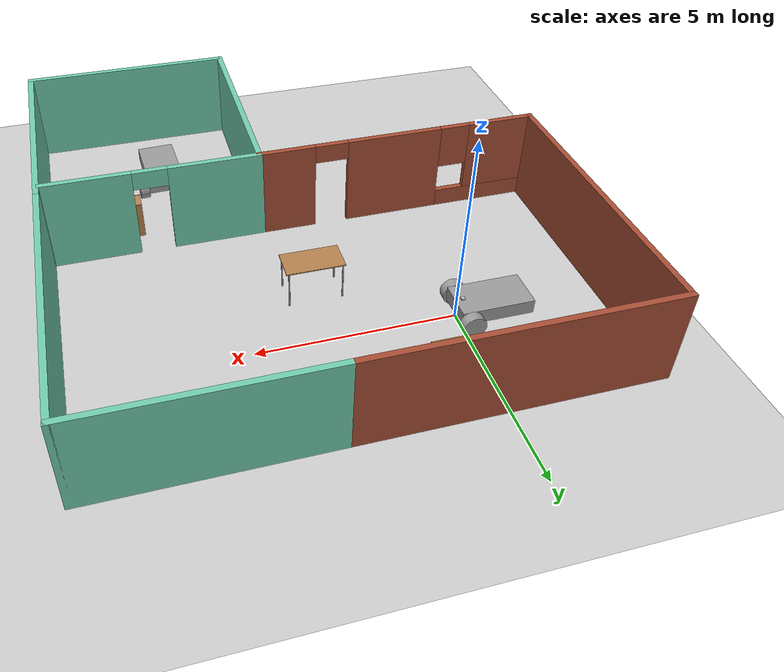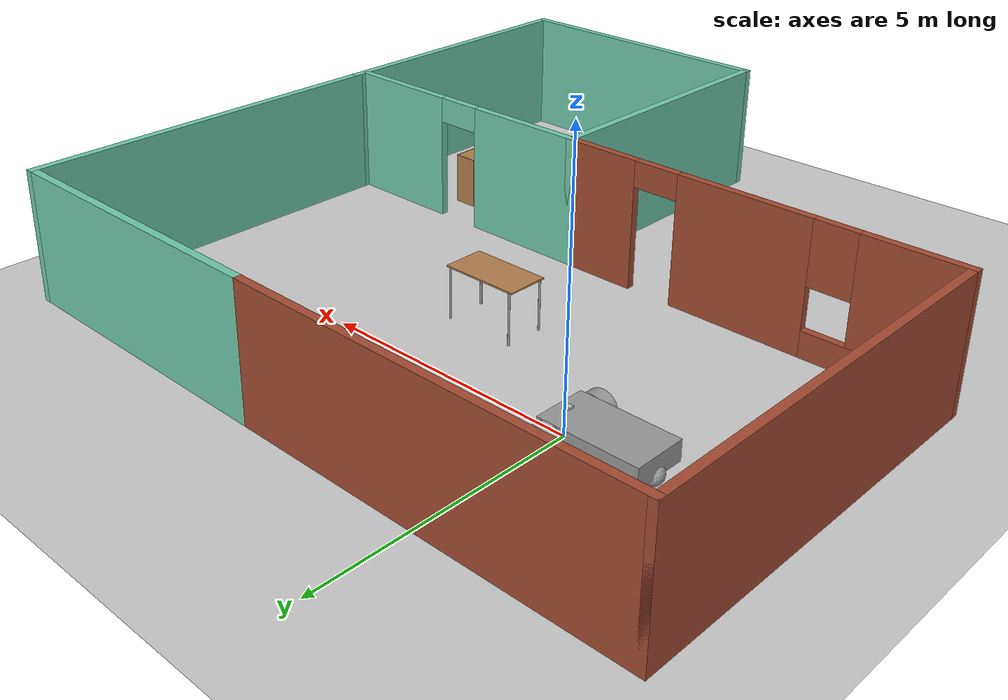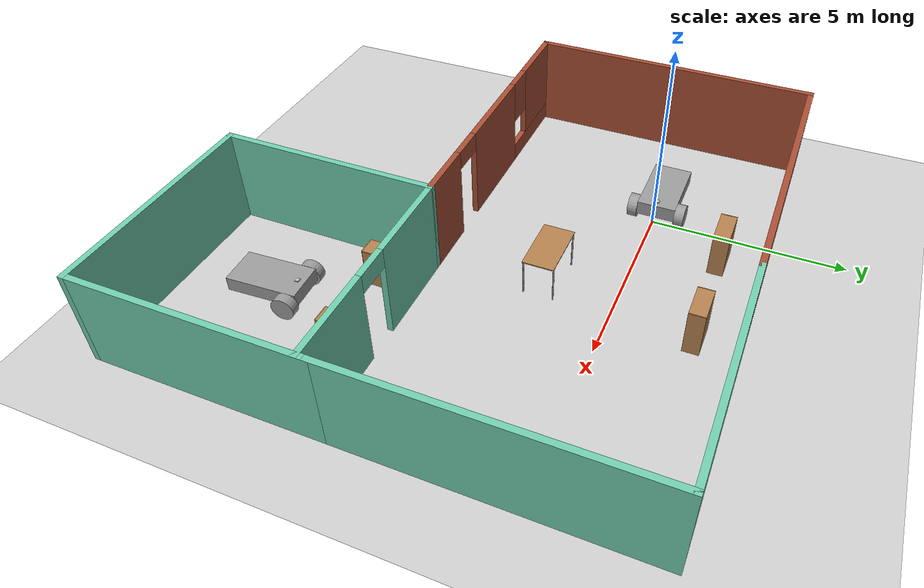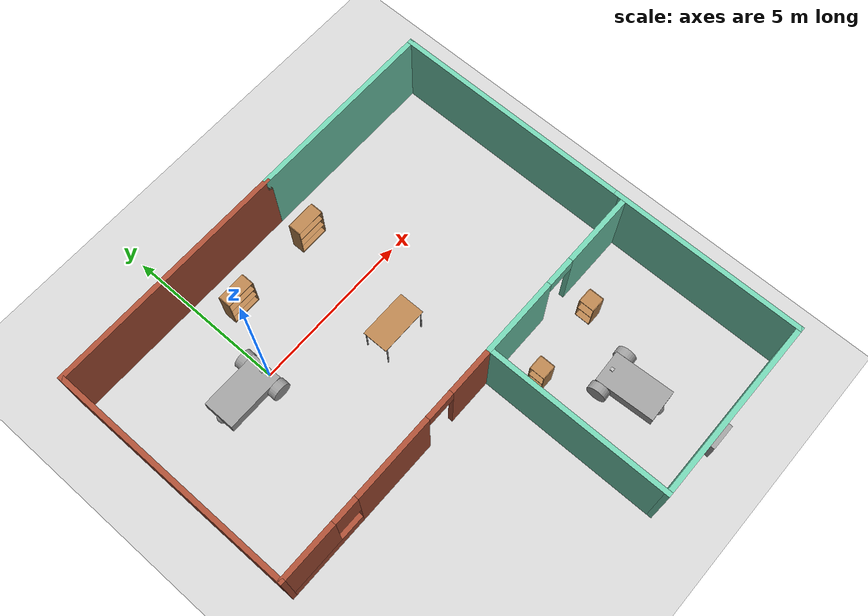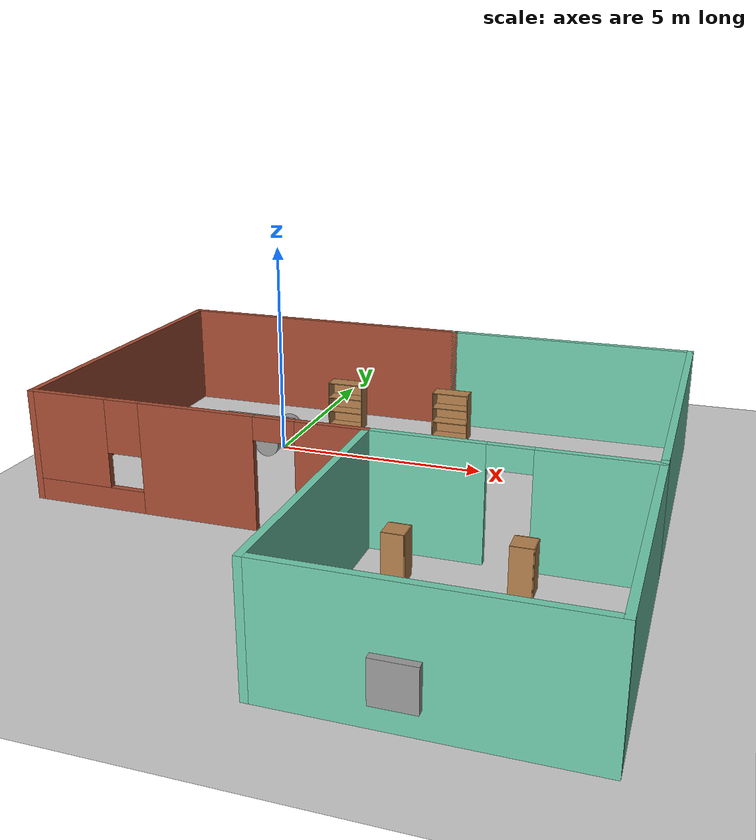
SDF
<sdf version="1.6">
 <world name="default">
  <plugin name="hello" filename="libhello.so"/>
  <light name="sun" type="directional">
   <pose>0 0 10 0 -0 0</pose>
   <diffuse>0.8 0.8 0.8 1</diffuse>
   <specular>0.2 0.2 0.2 1</specular>
   <attenuation>
    <range>1000</range>
    <constant>0.9</constant>
    <linear>0.01</linear>
    <quadratic>0.001</quadratic>
   </attenuation>
   <direction>-0.5 0.1 -0.9</direction>
  </light>
  <model name="ground_plane">
   <static>1</static>
   <link name="link">
    <collision name="collision">
     <geometry><plane><normal>0 0 1</normal><size>100 100</size></plane></geometry>
     <surface>
      <contact><collide_bitmask>65535</collide_bitmask></contact>
      <friction><ode><mu>100</mu><mu2>50</mu2></ode></friction>
     </surface>
    </collision>
    <visual name="visual">
     <cast_shadows>0</cast_shadows>
     <geometry><plane><normal>0 0 1</normal><size>100 100</size></plane></geometry>
     <material>
      <script><uri>file://media/materials/scripts/gazebo.material</uri><name>Gazebo/Grey</name></script>
     </material>
    </visual>
   </link>
  </model>
  <gravity>0 0 -9.8</gravity>
  <magnetic_field>6e-06 2.3e-05 -4.2e-05</magnetic_field>
  <atmosphere type="adiabatic"/>
  <physics name="default_physics" default="0" type="ode">
   <max_step_size>0.001</max_step_size>
   <real_time_factor>1</real_time_factor>
   <real_time_update_rate>1000</real_time_update_rate>
  </physics>
  <scene><ambient>0.4 0.4 0.4 1</ambient><background>0.7 0.7 0.7 1</background><shadows>1</shadows></scene>
  <audio><device>default</device></audio>
  <spherical_coordinates>
   <surface_model>EARTH_WGS84</surface_model>
   <latitude_deg>0</latitude_deg>
   <longitude_deg>0</longitude_deg>
   <elevation>0</elevation>
   <heading_deg>0</heading_deg>
  </spherical_coordinates>
  <model name="Building">
   <link name="Wall_0">
    <pose>-2.925 6.6 0 0 -0 0</pose>
    <visual name="Wall_0_Visual">
     <pose>0 0 1.25 0 -0 0</pose>
     <geometry><box><size>7.5 0.15 2.5</size></box></geometry>
     <material>
      <script><uri>file://media/materials/scripts/gazebo.material</uri><name>Gazebo/Bricks</name></script>
      <ambient>1 1 1 1</ambient>
     </material>
     <meta><layer>0</layer></meta>
    </visual>
    <collision name="Wall_0_Collision">
     <pose>0 0 1.25 0 -0 0</pose>
     <geometry><box><size>7.5 0.15 2.5</size></box></geometry>
     <surface>
      <friction>
       <ode><mu>1</mu><mu2>1</mu2><fdir1>0 0 0</fdir1><slip1>0</slip1><slip2>0</slip2></ode>
       <torsional>
        <coefficient>1</coefficient>
        <patch_radius>0</patch_radius>
        <surface_radius>0</surface_radius>
        <use_patch_radius>1</use_patch_radius>
        <ode><slip>0</slip></ode>
       </torsional>
      </friction>
      <bounce><restitution_coefficient>0</restitution_coefficient><threshold>1e+06</threshold></bounce>
      <contact>
       <collide_without_contact>0</collide_without_contact>
       <collide_without_contact_bitmask>1</collide_without_contact_bitmask>
       <collide_bitmask>1</collide_bitmask>
       <ode>
        <soft_cfm>0</soft_cfm>
        <soft_erp>0.2</soft_erp>
        <kp>1e+13</kp>
        <kd>1</kd>
        <max_vel>0.01</max_vel>
        <min_depth>0</min_depth>
       </ode>
       <bullet>
        <split_impulse>1</split_impulse>
        <split_impulse_penetration_threshold>-0.01</split_impulse_penetration_threshold>
        <soft_cfm>0</soft_cfm>
        <soft_erp>0.2</soft_erp>
        <kp>1e+13</kp>
        <kd>1</kd>
       </bullet>
      </contact>
     </surface>
    </collision>
   </link>
   <link name="Wall_1">
    <pose>3.675 6.6 0 0 -0 0</pose>
    <visual name="Wall_1_Visual">
     <pose>0 0 1.25 0 -0 0</pose>
     <geometry><box><size>6 0.15 2.5</size></box></geometry>
     <material>
      <script><uri>file://media/materials/scripts/gazebo.material</uri><name>Gazebo/Grey</name></script>
      <ambient>0.435294 0.796078 0.67451 1</ambient>
     </material>
     <meta><layer>0</layer></meta>
    </visual>
    <collision name="Wall_1_Collision">
     <pose>0 0 1.25 0 -0 0</pose>
     <geometry><box><size>6 0.15 2.5</size></box></geometry>
     <surface>
      <friction>
       <ode><mu>1</mu><mu2>1</mu2><fdir1>0 0 0</fdir1><slip1>0</slip1><slip2>0</slip2></ode>
       <torsional>
        <coefficient>1</coefficient>
        <patch_radius>0</patch_radius>
        <surface_radius>0</surface_radius>
        <use_patch_radius>1</use_patch_radius>
        <ode><slip>0</slip></ode>
       </torsional>
      </friction>
      <bounce><restitution_coefficient>0</restitution_coefficient><threshold>1e+06</threshold></bounce>
      <contact>
       <collide_without_contact>0</collide_without_contact>
       <collide_without_contact_bitmask>1</collide_without_contact_bitmask>
       <collide_bitmask>1</collide_bitmask>
       <ode>
        <soft_cfm>0</soft_cfm>
        <soft_erp>0.2</soft_erp>
        <kp>1e+13</kp>
        <kd>1</kd>
        <max_vel>0.01</max_vel>
        <min_depth>0</min_depth>
       </ode>
       <bullet>
        <split_impulse>1</split_impulse>
        <split_impulse_penetration_threshold>-0.01</split_impulse_penetration_threshold>
        <soft_cfm>0</soft_cfm>
        <soft_erp>0.2</soft_erp>
        <kp>1e+13</kp>
        <kd>1</kd>
       </bullet>
      </contact>
     </surface>
    </collision>
   </link>
   <link name="Wall_14">
    <pose>3.8 -1 0 0 -0 0</pose>
    <visual name="Wall_14_Visual_2">
     <pose>0.031268 0 2.25 0 -0 0</pose>
     <geometry><box><size>0.9 0.15 0.5</size></box></geometry>
     <material>
      <script><uri>file://media/materials/scripts/gazebo.material</uri><name>Gazebo/Grey</name></script>
      <ambient>0.435294 0.796078 0.67451 1</ambient>
     </material>
     <meta><layer>0</layer></meta>
    </visual>
    <visual name="Wall_14_Visual_0">
     <pose>-1.64687 0 1.25 0 -0 0</pose>
     <geometry><box><size>2.45627 0.15 2.5</size></box></geometry>
     <material>
      <script><uri>file://media/materials/scripts/gazebo.material</uri><name>Gazebo/Grey</name></script>
      <ambient>0.435294 0.796078 0.67451 1</ambient>
     </material>
     <meta><layer>0</layer></meta>
    </visual>
    <visual name="Wall_14_Visual_1">
     <pose>1.67813 0 1.25 0 -0 0</pose>
     <geometry><box><size>2.39373 0.15 2.5</size></box></geometry>
     <material>
      <script><uri>file://media/materials/scripts/gazebo.material</uri><name>Gazebo/Grey</name></script>
      <ambient>0.435294 0.796078 0.67451 1</ambient>
     </material>
     <meta><layer>0</layer></meta>
    </visual>
    <collision name="Wall_14_Collision_0">
     <pose>-1.64687 0 1.25 0 -0 0</pose>
     <geometry><box><size>2.45627 0.15 2.5</size></box></geometry>
     <surface>
      <friction>
       <ode><mu>1</mu><mu2>1</mu2><fdir1>0 0 0</fdir1><slip1>0</slip1><slip2>0</slip2></ode>
       <torsional>
        <coefficient>1</coefficient>
        <patch_radius>0</patch_radius>
        <surface_radius>0</surface_radius>
        <use_patch_radius>1</use_patch_radius>
        <ode><slip>0</slip></ode>
       </torsional>
      </friction>
      <bounce><restitution_coefficient>0</restitution_coefficient><threshold>1e+06</threshold></bounce>
      <contact>
       <collide_without_contact>0</collide_without_contact>
       <collide_without_contact_bitmask>1</collide_without_contact_bitmask>
       <collide_bitmask>1</collide_bitmask>
       <ode>
        <soft_cfm>0</soft_cfm>
        <soft_erp>0.2</soft_erp>
        <kp>1e+13</kp>
        <kd>1</kd>
        <max_vel>0.01</max_vel>
        <min_depth>0</min_depth>
       </ode>
       <bullet>
        <split_impulse>1</split_impulse>
        <split_impulse_penetration_threshold>-0.01</split_impulse_penetration_threshold>
        <soft_cfm>0</soft_cfm>
        <soft_erp>0.2</soft_erp>
        <kp>1e+13</kp>
        <kd>1</kd>
       </bullet>
      </contact>
     </surface>
    </collision>
    <collision name="Wall_14_Collision_1">
     <pose>1.67813 0 1.25 0 -0 0</pose>
     <geometry><box><size>2.39373 0.15 2.5</size></box></geometry>
     <surface>
      <friction>
       <ode><mu>1</mu><mu2>1</mu2><fdir1>0 0 0</fdir1><slip1>0</slip1><slip2>0</slip2></ode>
       <torsional>
        <coefficient>1</coefficient>
        <patch_radius>0</patch_radius>
        <surface_radius>0</surface_radius>
        <use_patch_radius>1</use_patch_radius>
        <ode><slip>0</slip></ode>
       </torsional>
      </friction>
      <bounce><restitution_coefficient>0</restitution_coefficient><threshold>1e+06</threshold></bounce>
      <contact>
       <collide_without_contact>0</collide_without_contact>
       <collide_without_contact_bitmask>1</collide_without_contact_bitmask>
       <collide_bitmask>1</collide_bitmask>
       <ode>
        <soft_cfm>0</soft_cfm>
        <soft_erp>0.2</soft_erp>
        <kp>1e+13</kp>
        <kd>1</kd>
        <max_vel>0.01</max_vel>
        <min_depth>0</min_depth>
       </ode>
       <bullet>
        <split_impulse>1</split_impulse>
        <split_impulse_penetration_threshold>-0.01</split_impulse_penetration_threshold>
        <soft_cfm>0</soft_cfm>
        <soft_erp>0.2</soft_erp>
        <kp>1e+13</kp>
        <kd>1</kd>
       </bullet>
      </contact>
     </surface>
    </collision>
    <collision name="Wall_14_Collision_2">
     <pose>0.031268 0 2.25 0 -0 0</pose>
     <geometry><box><size>0.9 0.15 0.5</size></box></geometry>
     <surface>
      <friction>
       <ode><mu>1</mu><mu2>1</mu2><fdir1>0 0 0</fdir1><slip1>0</slip1><slip2>0</slip2></ode>
       <torsional>
        <coefficient>1</coefficient>
        <patch_radius>0</patch_radius>
        <surface_radius>0</surface_radius>
        <use_patch_radius>1</use_patch_radius>
        <ode><slip>0</slip></ode>
       </torsional>
      </friction>
      <bounce><restitution_coefficient>0</restitution_coefficient><threshold>1e+06</threshold></bounce>
      <contact>
       <collide_without_contact>0</collide_without_contact>
       <collide_without_contact_bitmask>1</collide_without_contact_bitmask>
       <collide_bitmask>1</collide_bitmask>
       <ode>
        <soft_cfm>0</soft_cfm>
        <soft_erp>0.2</soft_erp>
        <kp>1e+13</kp>
        <kd>1</kd>
        <max_vel>0.01</max_vel>
        <min_depth>0</min_depth>
       </ode>
       <bullet>
        <split_impulse>1</split_impulse>
        <split_impulse_penetration_threshold>-0.01</split_impulse_penetration_threshold>
        <soft_cfm>0</soft_cfm>
        <soft_erp>0.2</soft_erp>
        <kp>1e+13</kp>
        <kd>1</kd>
       </bullet>
      </contact>
     </surface>
    </collision>
   </link>
   <link name="Wall_2">
    <pose>6.6 2.925 0 0 0 -1.5708</pose>
    <visual name="Wall_2_Visual">
     <pose>0 0 1.25 0 -0 0</pose>
     <geometry><box><size>7.5 0.15 2.5</size></box></geometry>
     <material>
      <script><uri>file://media/materials/scripts/gazebo.material</uri><name>Gazebo/Grey</name></script>
      <ambient>0.435294 0.796078 0.67451 1</ambient>
     </material>
     <meta><layer>0</layer></meta>
    </visual>
    <collision name="Wall_2_Collision">
     <pose>0 0 1.25 0 -0 0</pose>
     <geometry><box><size>7.5 0.15 2.5</size></box></geometry>
     <surface>
      <friction>
       <ode><mu>1</mu><mu2>1</mu2><fdir1>0 0 0</fdir1><slip1>0</slip1><slip2>0</slip2></ode>
       <torsional>
        <coefficient>1</coefficient>
        <patch_radius>0</patch_radius>
        <surface_radius>0</surface_radius>
        <use_patch_radius>1</use_patch_radius>
        <ode><slip>0</slip></ode>
       </torsional>
      </friction>
      <bounce><restitution_coefficient>0</restitution_coefficient><threshold>1e+06</threshold></bounce>
      <contact>
       <collide_without_contact>0</collide_without_contact>
       <collide_without_contact_bitmask>1</collide_without_contact_bitmask>
       <collide_bitmask>1</collide_bitmask>
       <ode>
        <soft_cfm>0</soft_cfm>
        <soft_erp>0.2</soft_erp>
        <kp>1e+13</kp>
        <kd>1</kd>
        <max_vel>0.01</max_vel>
        <min_depth>0</min_depth>
       </ode>
       <bullet>
        <split_impulse>1</split_impulse>
        <split_impulse_penetration_threshold>-0.01</split_impulse_penetration_threshold>
        <soft_cfm>0</soft_cfm>
        <soft_erp>0.2</soft_erp>
        <kp>1e+13</kp>
        <kd>1</kd>
       </bullet>
      </contact>
     </surface>
    </collision>
   </link>
   <link name="Wall_3">
    <pose>6.6 -3.675 0 0 0 -1.5708</pose>
    <visual name="Wall_3_Visual">
     <pose>0 0 1.25 0 -0 0</pose>
     <geometry><box><size>6 0.15 2.5</size></box></geometry>
     <material>
      <script><uri>file://media/materials/scripts/gazebo.material</uri><name>Gazebo/Grey</name></script>
      <ambient>0.435294 0.796078 0.67451 1</ambient>
     </material>
     <meta><layer>0</layer></meta>
    </visual>
    <collision name="Wall_3_Collision">
     <pose>0 0 1.25 0 -0 0</pose>
     <geometry><box><size>6 0.15 2.5</size></box></geometry>
     <surface>
      <friction>
       <ode><mu>1</mu><mu2>1</mu2><fdir1>0 0 0</fdir1><slip1>0</slip1><slip2>0</slip2></ode>
       <torsional>
        <coefficient>1</coefficient>
        <patch_radius>0</patch_radius>
        <surface_radius>0</surface_radius>
        <use_patch_radius>1</use_patch_radius>
        <ode><slip>0</slip></ode>
       </torsional>
      </friction>
      <bounce><restitution_coefficient>0</restitution_coefficient><threshold>1e+06</threshold></bounce>
      <contact>
       <collide_without_contact>0</collide_without_contact>
       <collide_without_contact_bitmask>1</collide_without_contact_bitmask>
       <collide_bitmask>1</collide_bitmask>
       <ode>
        <soft_cfm>0</soft_cfm>
        <soft_erp>0.2</soft_erp>
        <kp>1e+13</kp>
        <kd>1</kd>
        <max_vel>0.01</max_vel>
        <min_depth>0</min_depth>
       </ode>
       <bullet>
        <split_impulse>1</split_impulse>
        <split_impulse_penetration_threshold>-0.01</split_impulse_penetration_threshold>
        <soft_cfm>0</soft_cfm>
        <soft_erp>0.2</soft_erp>
        <kp>1e+13</kp>
        <kd>1</kd>
       </bullet>
      </contact>
     </surface>
    </collision>
   </link>
   <link name="Wall_4">
    <pose>3.8 -6.6 0 0 -0 3.14159</pose>
    <visual name="Wall_4_Visual">
     <pose>0 0 1.25 0 -0 0</pose>
     <geometry><box><size>5.75 0.15 2.5</size></box></geometry>
     <material>
      <script><uri>file://media/materials/scripts/gazebo.material</uri><name>Gazebo/Grey</name></script>
      <ambient>0.435294 0.796078 0.67451 1</ambient>
     </material>
     <meta><layer>0</layer></meta>
    </visual>
    <collision name="Wall_4_Collision">
     <pose>0 0 1.25 0 -0 0</pose>
     <geometry><box><size>5.75 0.15 2.5</size></box></geometry>
     <surface>
      <friction>
       <ode><mu>1</mu><mu2>1</mu2><fdir1>0 0 0</fdir1><slip1>0</slip1><slip2>0</slip2></ode>
       <torsional>
        <coefficient>1</coefficient>
        <patch_radius>0</patch_radius>
        <surface_radius>0</surface_radius>
        <use_patch_radius>1</use_patch_radius>
        <ode><slip>0</slip></ode>
       </torsional>
      </friction>
      <bounce><restitution_coefficient>0</restitution_coefficient><threshold>1e+06</threshold></bounce>
      <contact>
       <collide_without_contact>0</collide_without_contact>
       <collide_without_contact_bitmask>1</collide_without_contact_bitmask>
       <collide_bitmask>1</collide_bitmask>
       <ode>
        <soft_cfm>0</soft_cfm>
        <soft_erp>0.2</soft_erp>
        <kp>1e+13</kp>
        <kd>1</kd>
        <max_vel>0.01</max_vel>
        <min_depth>0</min_depth>
       </ode>
       <bullet>
        <split_impulse>1</split_impulse>
        <split_impulse_penetration_threshold>-0.01</split_impulse_penetration_threshold>
        <soft_cfm>0</soft_cfm>
        <soft_erp>0.2</soft_erp>
        <kp>1e+13</kp>
        <kd>1</kd>
       </bullet>
      </contact>
     </surface>
    </collision>
   </link>
   <link name="Wall_5">
    <pose>1 -3.8 0 0 -0 1.5708</pose>
    <visual name="Wall_5_Visual">
     <pose>0 0 1.25 0 -0 0</pose>
     <geometry><box><size>5.75 0.15 2.5</size></box></geometry>
     <material>
      <script><uri>file://media/materials/scripts/gazebo.material</uri><name>Gazebo/Grey</name></script>
      <ambient>0.435294 0.796078 0.67451 1</ambient>
     </material>
     <meta><layer>0</layer></meta>
    </visual>
    <collision name="Wall_5_Collision">
     <pose>0 0 1.25 0 -0 0</pose>
     <geometry><box><size>5.75 0.15 2.5</size></box></geometry>
     <surface>
      <friction>
       <ode><mu>1</mu><mu2>1</mu2><fdir1>0 0 0</fdir1><slip1>0</slip1><slip2>0</slip2></ode>
       <torsional>
        <coefficient>1</coefficient>
        <patch_radius>0</patch_radius>
        <surface_radius>0</surface_radius>
        <use_patch_radius>1</use_patch_radius>
        <ode><slip>0</slip></ode>
       </torsional>
      </friction>
      <bounce><restitution_coefficient>0</restitution_coefficient><threshold>1e+06</threshold></bounce>
      <contact>
       <collide_without_contact>0</collide_without_contact>
       <collide_without_contact_bitmask>1</collide_without_contact_bitmask>
       <collide_bitmask>1</collide_bitmask>
       <ode>
        <soft_cfm>0</soft_cfm>
        <soft_erp>0.2</soft_erp>
        <kp>1e+13</kp>
        <kd>1</kd>
        <max_vel>0.01</max_vel>
        <min_depth>0</min_depth>
       </ode>
       <bullet>
        <split_impulse>1</split_impulse>
        <split_impulse_penetration_threshold>-0.01</split_impulse_penetration_threshold>
        <soft_cfm>0</soft_cfm>
        <soft_erp>0.2</soft_erp>
        <kp>1e+13</kp>
        <kd>1</kd>
       </bullet>
      </contact>
     </surface>
    </collision>
   </link>
   <link name="Wall_6">
    <pose>-2.8 -1 0 0 -0 3.14159</pose>
    <visual name="Wall_6_Visual_0">
     <pose>-3.0921 0 1.25 0 -0 0</pose>
     <geometry><box><size>1.56581 0.15 2.5</size></box></geometry>
     <material>
      <script><uri>file://media/materials/scripts/gazebo.material</uri><name>Gazebo/Bricks</name></script>
      <ambient>1 1 1 1</ambient>
     </material>
     <meta><layer>0</layer></meta>
    </visual>
    <visual name="Wall_6_Visual_1">
     <pose>-0.105844 0 1.25 0 -0 0</pose>
     <geometry><box><size>2.6067 0.15 2.5</size></box></geometry>
     <material>
      <script><uri>file://media/materials/scripts/gazebo.material</uri><name>Gazebo/Bricks</name></script>
      <ambient>1 1 1 1</ambient>
     </material>
     <meta><layer>0</layer></meta>
    </visual>
    <visual name="Wall_6_Visual_2">
     <pose>2.53625 0 0.25 0 -0 0</pose>
     <geometry><box><size>2.6775 0.15 0.5</size></box></geometry>
     <material>
      <script><uri>file://media/materials/scripts/gazebo.material</uri><name>Gazebo/Bricks</name></script>
      <ambient>1 1 1 1</ambient>
     </material>
     <meta><layer>0</layer></meta>
    </visual>
    <visual name="Wall_6_Visual_3">
     <pose>2.93625 0 1.5 0 -0 0</pose>
     <geometry><box><size>1.8775 0.15 2</size></box></geometry>
     <material>
      <script><uri>file://media/materials/scripts/gazebo.material</uri><name>Gazebo/Bricks</name></script>
      <ambient>1 1 1 1</ambient>
     </material>
     <meta><layer>0</layer></meta>
    </visual>
    <visual name="Wall_6_Visual_4">
     <pose>1.5975 0 1.9 0 -0 0</pose>
     <geometry><box><size>0.8 0.15 1.2</size></box></geometry>
     <material>
      <script><uri>file://media/materials/scripts/gazebo.material</uri><name>Gazebo/Bricks</name></script>
      <ambient>1 1 1 1</ambient>
     </material>
     <meta><layer>0</layer></meta>
    </visual>
    <visual name="Wall_6_Visual_5">
     <pose>-1.85919 0 2.25 0 -0 0</pose>
     <geometry><box><size>0.9 0.15 0.5</size></box></geometry>
     <material>
      <script><uri>file://media/materials/scripts/gazebo.material</uri><name>Gazebo/Bricks</name></script>
      <ambient>1 1 1 1</ambient>
     </material>
     <meta><layer>0</layer></meta>
    </visual>
    <collision name="Wall_6_Collision_0">
     <pose>-3.0921 0 1.25 0 -0 0</pose>
     <geometry><box><size>1.56581 0.15 2.5</size></box></geometry>
     <surface>
      <friction>
       <ode><mu>1</mu><mu2>1</mu2><fdir1>0 0 0</fdir1><slip1>0</slip1><slip2>0</slip2></ode>
       <torsional>
        <coefficient>1</coefficient>
        <patch_radius>0</patch_radius>
        <surface_radius>0</surface_radius>
        <use_patch_radius>1</use_patch_radius>
        <ode><slip>0</slip></ode>
       </torsional>
      </friction>
      <bounce><restitution_coefficient>0</restitution_coefficient><threshold>1e+06</threshold></bounce>
      <contact>
       <collide_without_contact>0</collide_without_contact>
       <collide_without_contact_bitmask>1</collide_without_contact_bitmask>
       <collide_bitmask>1</collide_bitmask>
       <ode>
        <soft_cfm>0</soft_cfm>
        <soft_erp>0.2</soft_erp>
        <kp>1e+13</kp>
        <kd>1</kd>
        <max_vel>0.01</max_vel>
        <min_depth>0</min_depth>
       </ode>
       <bullet>
        <split_impulse>1</split_impulse>
        <split_impulse_penetration_threshold>-0.01</split_impulse_penetration_threshold>
        <soft_cfm>0</soft_cfm>
        <soft_erp>0.2</soft_erp>
        <kp>1e+13</kp>
        <kd>1</kd>
       </bullet>
      </contact>
     </surface>
    </collision>
    <collision name="Wall_6_Collision_1">
     <pose>-0.105844 0 1.25 0 -0 0</pose>
     <geometry><box><size>2.6067 0.15 2.5</size></box></geometry>
     <surface>
      <friction>
       <ode><mu>1</mu><mu2>1</mu2><fdir1>0 0 0</fdir1><slip1>0</slip1><slip2>0</slip2></ode>
       <torsional>
        <coefficient>1</coefficient>
        <patch_radius>0</patch_radius>
        <surface_radius>0</surface_radius>
        <use_patch_radius>1</use_patch_radius>
        <ode><slip>0</slip></ode>
       </torsional>
      </friction>
      <bounce><restitution_coefficient>0</restitution_coefficient><threshold>1e+06</threshold></bounce>
      <contact>
       <collide_without_contact>0</collide_without_contact>
       <collide_without_contact_bitmask>1</collide_without_contact_bitmask>
       <collide_bitmask>1</collide_bitmask>
       <ode>
        <soft_cfm>0</soft_cfm>
        <soft_erp>0.2</soft_erp>
        <kp>1e+13</kp>
        <kd>1</kd>
        <max_vel>0.01</max_vel>
        <min_depth>0</min_depth>
       </ode>
       <bullet>
        <split_impulse>1</split_impulse>
        <split_impulse_penetration_threshold>-0.01</split_impulse_penetration_threshold>
        <soft_cfm>0</soft_cfm>
        <soft_erp>0.2</soft_erp>
        <kp>1e+13</kp>
        <kd>1</kd>
       </bullet>
      </contact>
     </surface>
    </collision>
    <collision name="Wall_6_Collision_2">
     <pose>2.53625 0 0.25 0 -0 0</pose>
     <geometry><box><size>2.6775 0.15 0.5</size></box></geometry>
     <surface>
      <friction>
       <ode><mu>1</mu><mu2>1</mu2><fdir1>0 0 0</fdir1><slip1>0</slip1><slip2>0</slip2></ode>
       <torsional>
        <coefficient>1</coefficient>
        <patch_radius>0</patch_radius>
        <surface_radius>0</surface_radius>
        <use_patch_radius>1</use_patch_radius>
        <ode><slip>0</slip></ode>
       </torsional>
      </friction>
      <bounce><restitution_coefficient>0</restitution_coefficient><threshold>1e+06</threshold></bounce>
      <contact>
       <collide_without_contact>0</collide_without_contact>
       <collide_without_contact_bitmask>1</collide_without_contact_bitmask>
       <collide_bitmask>1</collide_bitmask>
       <ode>
        <soft_cfm>0</soft_cfm>
        <soft_erp>0.2</soft_erp>
        <kp>1e+13</kp>
        <kd>1</kd>
        <max_vel>0.01</max_vel>
        <min_depth>0</min_depth>
       </ode>
       <bullet>
        <split_impulse>1</split_impulse>
        <split_impulse_penetration_threshold>-0.01</split_impulse_penetration_threshold>
        <soft_cfm>0</soft_cfm>
        <soft_erp>0.2</soft_erp>
        <kp>1e+13</kp>
        <kd>1</kd>
       </bullet>
      </contact>
     </surface>
    </collision>
    <collision name="Wall_6_Collision_4">
     <pose>1.5975 0 1.9 0 -0 0</pose>
     <geometry><box><size>0.8 0.15 1.2</size></box></geometry>
     <surface>
      <friction>
       <ode><mu>1</mu><mu2>1</mu2><fdir1>0 0 0</fdir1><slip1>0</slip1><slip2>0</slip2></ode>
       <torsional>
        <coefficient>1</coefficient>
        <patch_radius>0</patch_radius>
        <surface_radius>0</surface_radius>
        <use_patch_radius>1</use_patch_radius>
        <ode><slip>0</slip></ode>
       </torsional>
      </friction>
      <bounce><restitution_coefficient>0</restitution_coefficient><threshold>1e+06</threshold></bounce>
      <contact>
       <collide_without_contact>0</collide_without_contact>
       <collide_without_contact_bitmask>1</collide_without_contact_bitmask>
       <collide_bitmask>1</collide_bitmask>
       <ode>
        <soft_cfm>0</soft_cfm>
        <soft_erp>0.2</soft_erp>
        <kp>1e+13</kp>
        <kd>1</kd>
        <max_vel>0.01</max_vel>
        <min_depth>0</min_depth>
       </ode>
       <bullet>
        <split_impulse>1</split_impulse>
        <split_impulse_penetration_threshold>-0.01</split_impulse_penetration_threshold>
        <soft_cfm>0</soft_cfm>
        <soft_erp>0.2</soft_erp>
        <kp>1e+13</kp>
        <kd>1</kd>
       </bullet>
      </contact>
     </surface>
    </collision>
    <collision name="Wall_6_Collision_3">
     <pose>2.93625 0 1.5 0 -0 0</pose>
     <geometry><box><size>1.8775 0.15 2</size></box></geometry>
     <surface>
      <friction>
       <ode><mu>1</mu><mu2>1</mu2><fdir1>0 0 0</fdir1><slip1>0</slip1><slip2>0</slip2></ode>
       <torsional>
        <coefficient>1</coefficient>
        <patch_radius>0</patch_radius>
        <surface_radius>0</surface_radius>
        <use_patch_radius>1</use_patch_radius>
        <ode><slip>0</slip></ode>
       </torsional>
      </friction>
      <bounce><restitution_coefficient>0</restitution_coefficient><threshold>1e+06</threshold></bounce>
      <contact>
       <collide_without_contact>0</collide_without_contact>
       <collide_without_contact_bitmask>1</collide_without_contact_bitmask>
       <collide_bitmask>1</collide_bitmask>
       <ode>
        <soft_cfm>0</soft_cfm>
        <soft_erp>0.2</soft_erp>
        <kp>1e+13</kp>
        <kd>1</kd>
        <max_vel>0.01</max_vel>
        <min_depth>0</min_depth>
       </ode>
       <bullet>
        <split_impulse>1</split_impulse>
        <split_impulse_penetration_threshold>-0.01</split_impulse_penetration_threshold>
        <soft_cfm>0</soft_cfm>
        <soft_erp>0.2</soft_erp>
        <kp>1e+13</kp>
        <kd>1</kd>
       </bullet>
      </contact>
     </surface>
    </collision>
    <collision name="Wall_6_Collision_5">
     <pose>-1.85919 0 2.25 0 -0 0</pose>
     <geometry><box><size>0.9 0.15 0.5</size></box></geometry>
     <surface>
      <friction>
       <ode><mu>1</mu><mu2>1</mu2><fdir1>0 0 0</fdir1><slip1>0</slip1><slip2>0</slip2></ode>
       <torsional>
        <coefficient>1</coefficient>
        <patch_radius>0</patch_radius>
        <surface_radius>0</surface_radius>
        <use_patch_radius>1</use_patch_radius>
        <ode><slip>0</slip></ode>
       </torsional>
      </friction>
      <bounce><restitution_coefficient>0</restitution_coefficient><threshold>1e+06</threshold></bounce>
      <contact>
       <collide_without_contact>0</collide_without_contact>
       <collide_without_contact_bitmask>1</collide_without_contact_bitmask>
       <collide_bitmask>1</collide_bitmask>
       <ode>
        <soft_cfm>0</soft_cfm>
        <soft_erp>0.2</soft_erp>
        <kp>1e+13</kp>
        <kd>1</kd>
        <max_vel>0.01</max_vel>
        <min_depth>0</min_depth>
       </ode>
       <bullet>
        <split_impulse>1</split_impulse>
        <split_impulse_penetration_threshold>-0.01</split_impulse_penetration_threshold>
        <soft_cfm>0</soft_cfm>
        <soft_erp>0.2</soft_erp>
        <kp>1e+13</kp>
        <kd>1</kd>
       </bullet>
      </contact>
     </surface>
    </collision>
   </link>
   <link name="Wall_7">
    <pose>-6.6 2.8 0 0 -0 1.5708</pose>
    <visual name="Wall_7_Visual">
     <pose>0 0 1.25 0 -0 0</pose>
     <geometry><box><size>7.75 0.15 2.5</size></box></geometry>
     <material>
      <script><uri>file://media/materials/scripts/gazebo.material</uri><name>Gazebo/Bricks</name></script>
      <ambient>1 1 1 1</ambient>
     </material>
     <meta><layer>0</layer></meta>
    </visual>
    <collision name="Wall_7_Collision">
     <pose>0 0 1.25 0 -0 0</pose>
     <geometry><box><size>7.75 0.15 2.5</size></box></geometry>
     <surface>
      <friction>
       <ode><mu>1</mu><mu2>1</mu2><fdir1>0 0 0</fdir1><slip1>0</slip1><slip2>0</slip2></ode>
       <torsional>
        <coefficient>1</coefficient>
        <patch_radius>0</patch_radius>
        <surface_radius>0</surface_radius>
        <use_patch_radius>1</use_patch_radius>
        <ode><slip>0</slip></ode>
       </torsional>
      </friction>
      <bounce><restitution_coefficient>0</restitution_coefficient><threshold>1e+06</threshold></bounce>
      <contact>
       <collide_without_contact>0</collide_without_contact>
       <collide_without_contact_bitmask>1</collide_without_contact_bitmask>
       <collide_bitmask>1</collide_bitmask>
       <ode>
        <soft_cfm>0</soft_cfm>
        <soft_erp>0.2</soft_erp>
        <kp>1e+13</kp>
        <kd>1</kd>
        <max_vel>0.01</max_vel>
        <min_depth>0</min_depth>
       </ode>
       <bullet>
        <split_impulse>1</split_impulse>
        <split_impulse_penetration_threshold>-0.01</split_impulse_penetration_threshold>
        <soft_cfm>0</soft_cfm>
        <soft_erp>0.2</soft_erp>
        <kp>1e+13</kp>
        <kd>1</kd>
       </bullet>
      </contact>
     </surface>
    </collision>
   </link>
   <link name="Window_1">
    <pose>3.43359 -6.73734 0.5 0 -0 0</pose>
    <visual name="Window_1_Visual">
     <pose>0 0 0.4 0 -0 0</pose>
     <geometry><box><size>0.8 0.17 0.8</size></box></geometry>
     <material>
      <script><uri>file://media/materials/scripts/gazebo.material</uri><name>Gazebo/Grey</name></script>
     </material>
    </visual>
    <collision name="Window_1_Collision">
     <pose>0 0 0.4 0 -0 0</pose>
     <geometry><box><size>0.8 0.17 0.8</size></box></geometry>
     <surface>
      <friction>
       <ode><mu>1</mu><mu2>1</mu2><fdir1>0 0 0</fdir1><slip1>0</slip1><slip2>0</slip2></ode>
       <torsional>
        <coefficient>1</coefficient>
        <patch_radius>0</patch_radius>
        <surface_radius>0</surface_radius>
        <use_patch_radius>1</use_patch_radius>
        <ode><slip>0</slip></ode>
       </torsional>
      </friction>
      <bounce><restitution_coefficient>0</restitution_coefficient><threshold>1e+06</threshold></bounce>
      <contact>
       <collide_without_contact>0</collide_without_contact>
       <collide_without_contact_bitmask>1</collide_without_contact_bitmask>
       <collide_bitmask>1</collide_bitmask>
       <ode>
        <soft_cfm>0</soft_cfm>
        <soft_erp>0.2</soft_erp>
        <kp>1e+13</kp>
        <kd>1</kd>
        <max_vel>0.01</max_vel>
        <min_depth>0</min_depth>
       </ode>
       <bullet>
        <split_impulse>1</split_impulse>
        <split_impulse_penetration_threshold>-0.01</split_impulse_penetration_threshold>
        <soft_cfm>0</soft_cfm>
        <soft_erp>0.2</soft_erp>
        <kp>1e+13</kp>
        <kd>1</kd>
       </bullet>
      </contact>
     </surface>
    </collision>
   </link>
   <static>1</static>
   <pose>2.78516 -3.53369 0 0 -0 0</pose>
  </model>
  <model name="Car">
   <link name="link_0">
    <inertial>
     <mass>0.688833</mass>
     <inertia>
      <ixx>0.0653771</ixx>
      <ixy>0</ixy>
      <ixz>0</ixz>
      <iyy>0.204042</iyy>
      <iyz>0</iyz>
      <izz>0.25347</izz>
     </inertia>
     <pose>0 0 0.2 0 -0 0</pose>
    </inertial>
    <pose>-0.006569 -0.057662 0.4 0 -0 0</pose>
    <visual name="visual">
     <geometry><box><size>1.84815 1 0.372719</size></box></geometry>
     <material>
      <lighting>1</lighting>
      <script><uri>file://media/materials/scripts/gazebo.material</uri><name>Gazebo/Grey</name></script>
      <shader type="vertex"><normal_map>__default__</normal_map></shader>
      <ambient>0.3 0.3 0.3 1</ambient>
      <diffuse>0.7 0.7 0.7 1</diffuse>
      <specular>0.01 0.01 0.01 1</specular>
      <emissive>0 0 0 1</emissive>
     </material>
    </visual>
    <collision name="collision">
     <geometry><box><size>1.84815 1 0.372719</size></box></geometry>
     <surface>
      <friction>
       <ode><mu>1</mu><mu2>1</mu2><fdir1>0 0 0</fdir1><slip1>0</slip1><slip2>0</slip2></ode>
       <torsional>
        <coefficient>1</coefficient>
        <patch_radius>0</patch_radius>
        <surface_radius>0</surface_radius>
        <use_patch_radius>1</use_patch_radius>
        <ode><slip>0</slip></ode>
       </torsional>
      </friction>
      <bounce><restitution_coefficient>0</restitution_coefficient><threshold>1e+06</threshold></bounce>
      <contact>
       <collide_without_contact>0</collide_without_contact>
       <collide_without_contact_bitmask>1</collide_without_contact_bitmask>
       <collide_bitmask>1</collide_bitmask>
       <ode>
        <soft_cfm>0</soft_cfm>
        <soft_erp>0.2</soft_erp>
        <kp>1e+13</kp>
        <kd>1</kd>
        <max_vel>0.01</max_vel>
        <min_depth>0</min_depth>
       </ode>
       <bullet>
        <split_impulse>1</split_impulse>
        <split_impulse_penetration_threshold>-0.01</split_impulse_penetration_threshold>
        <soft_cfm>0</soft_cfm>
        <soft_erp>0.2</soft_erp>
        <kp>1e+13</kp>
        <kd>1</kd>
       </bullet>
      </contact>
     </surface>
    </collision>
   </link>
   <link name="link_1">
    <inertial>
     <mass>1</mass>
     <inertia><ixx>0.145833</ixx><ixy>0</ixy><ixz>0</ixz><iyy>0.145833</iyy><iyz>0</iyz><izz>0.125</izz></inertia>
    </inertial>
    <pose>0.689747 -0.682691 0.3 1.5707 -0 0</pose>
    <visual name="visual">
     <geometry><cylinder><radius>0.3</radius><length>0.25</length></cylinder></geometry>
     <material>
      <lighting>1</lighting>
      <script><uri>file://media/materials/scripts/gazebo.material</uri><name>Gazebo/Grey</name></script>
      <shader type="vertex"><normal_map>__default__</normal_map></shader>
      <ambient>0.3 0.3 0.3 1</ambient>
      <diffuse>0.7 0.7 0.7 1</diffuse>
      <specular>0.01 0.01 0.01 1</specular>
      <emissive>0 0 0 1</emissive>
     </material>
    </visual>
    <collision name="collision">
     <geometry><cylinder><radius>0.3</radius><length>0.25</length></cylinder></geometry>
     <surface>
      <friction>
       <ode><mu>1</mu><mu2>1</mu2><fdir1>0 0 0</fdir1><slip1>0</slip1><slip2>0</slip2></ode>
       <torsional>
        <coefficient>1</coefficient>
        <patch_radius>0</patch_radius>
        <surface_radius>0</surface_radius>
        <use_patch_radius>1</use_patch_radius>
        <ode><slip>0</slip></ode>
       </torsional>
      </friction>
      <bounce><restitution_coefficient>0</restitution_coefficient><threshold>1e+06</threshold></bounce>
      <contact>
       <collide_without_contact>0</collide_without_contact>
       <collide_without_contact_bitmask>1</collide_without_contact_bitmask>
       <collide_bitmask>1</collide_bitmask>
       <ode>
        <soft_cfm>0</soft_cfm>
        <soft_erp>0.2</soft_erp>
        <kp>1e+13</kp>
        <kd>1</kd>
        <max_vel>0.01</max_vel>
        <min_depth>0</min_depth>
       </ode>
       <bullet>
        <split_impulse>1</split_impulse>
        <split_impulse_penetration_threshold>-0.01</split_impulse_penetration_threshold>
        <soft_cfm>0</soft_cfm>
        <soft_erp>0.2</soft_erp>
        <kp>1e+13</kp>
        <kd>1</kd>
       </bullet>
      </contact>
     </surface>
    </collision>
   </link>
   <link name="link_1_clone">
    <inertial>
     <mass>1</mass>
     <inertia><ixx>0.145833</ixx><ixy>0</ixy><ixz>0</ixz><iyy>0.145833</iyy><iyz>0</iyz><izz>0.125</izz></inertia>
    </inertial>
    <pose>0.689747 0.567367 0.3 1.5707 -0 0</pose>
    <visual name="visual">
     <geometry><cylinder><radius>0.3</radius><length>0.25</length></cylinder></geometry>
     <material>
      <lighting>1</lighting>
      <script><uri>file://media/materials/scripts/gazebo.material</uri><name>Gazebo/Grey</name></script>
      <shader type="vertex"><normal_map>__default__</normal_map></shader>
      <ambient>0.3 0.3 0.3 1</ambient>
      <diffuse>0.7 0.7 0.7 1</diffuse>
      <specular>0.01 0.01 0.01 1</specular>
      <emissive>0 0 0 1</emissive>
     </material>
    </visual>
    <collision name="collision">
     <geometry><cylinder><radius>0.3</radius><length>0.25</length></cylinder></geometry>
     <surface>
      <friction>
       <ode><mu>1</mu><mu2>1</mu2><fdir1>0 0 0</fdir1><slip1>0</slip1><slip2>0</slip2></ode>
       <torsional>
        <coefficient>1</coefficient>
        <patch_radius>0</patch_radius>
        <surface_radius>0</surface_radius>
        <use_patch_radius>1</use_patch_radius>
        <ode><slip>0</slip></ode>
       </torsional>
      </friction>
      <bounce><restitution_coefficient>0</restitution_coefficient><threshold>1e+06</threshold></bounce>
      <contact>
       <collide_without_contact>0</collide_without_contact>
       <collide_without_contact_bitmask>1</collide_without_contact_bitmask>
       <collide_bitmask>1</collide_bitmask>
       <ode>
        <soft_cfm>0</soft_cfm>
        <soft_erp>0.2</soft_erp>
        <kp>1e+13</kp>
        <kd>1</kd>
        <max_vel>0.01</max_vel>
        <min_depth>0</min_depth>
       </ode>
       <bullet>
        <split_impulse>1</split_impulse>
        <split_impulse_penetration_threshold>-0.01</split_impulse_penetration_threshold>
        <soft_cfm>0</soft_cfm>
        <soft_erp>0.2</soft_erp>
        <kp>1e+13</kp>
        <kd>1</kd>
       </bullet>
      </contact>
     </surface>
    </collision>
   </link>
   <link name="link_2">
    <inertial>
     <mass>1</mass>
     <inertia><ixx>0.1</ixx><ixy>0</ixy><ixz>0</ixz><iyy>0.1</iyy><iyz>0</iyz><izz>0.1</izz></inertia>
     <pose>0 0 0.2 0 -0 0</pose>
    </inertial>
    <pose>-0.802885 -0.057662 0.2 0 -0 0</pose>
    <visual name="visual">
     <geometry><sphere><radius>0.2</radius></sphere></geometry>
     <material>
      <lighting>1</lighting>
      <script><uri>file://media/materials/scripts/gazebo.material</uri><name>Gazebo/Grey</name></script>
      <shader type="vertex"><normal_map>__default__</normal_map></shader>
      <ambient>0.3 0.3 0.3 1</ambient>
      <diffuse>0.7 0.7 0.7 1</diffuse>
      <specular>0.01 0.01 0.01 1</specular>
      <emissive>0 0 0 1</emissive>
     </material>
    </visual>
    <collision name="collision">
     <geometry><sphere><radius>0.2</radius></sphere></geometry>
     <surface>
      <friction>
       <ode><mu>1</mu><mu2>1</mu2><fdir1>0 0 0</fdir1><slip1>0</slip1><slip2>0</slip2></ode>
       <torsional>
        <coefficient>1</coefficient>
        <patch_radius>0</patch_radius>
        <surface_radius>0</surface_radius>
        <use_patch_radius>1</use_patch_radius>
        <ode><slip>0</slip></ode>
       </torsional>
      </friction>
      <bounce><restitution_coefficient>0</restitution_coefficient><threshold>1e+06</threshold></bounce>
      <contact>
       <collide_without_contact>0</collide_without_contact>
       <collide_without_contact_bitmask>1</collide_without_contact_bitmask>
       <collide_bitmask>1</collide_bitmask>
       <ode>
        <soft_cfm>0</soft_cfm>
        <soft_erp>0.2</soft_erp>
        <kp>1e+13</kp>
        <kd>1</kd>
        <max_vel>0.01</max_vel>
        <min_depth>0</min_depth>
       </ode>
       <bullet>
        <split_impulse>1</split_impulse>
        <split_impulse_penetration_threshold>-0.01</split_impulse_penetration_threshold>
        <soft_cfm>0</soft_cfm>
        <soft_erp>0.2</soft_erp>
        <kp>1e+13</kp>
        <kd>1</kd>
       </bullet>
      </contact>
     </surface>
    </collision>
   </link>
   <model name="depth_camera">
    <link name="link">
     <pose>0 0 0.05 0 -0 0</pose>
     <inertial>
      <mass>0.1</mass>
      <inertia>
       <ixx>0.000166667</ixx>
       <iyy>0.000166667</iyy>
       <izz>0.000166667</izz>
       <ixy>0</ixy>
       <ixz>0</ixz>
       <iyz>0</iyz>
      </inertia>
     </inertial>
     <collision name="collision"><geometry><box><size>0.1 0.1 0.1</size></box></geometry></collision>
     <visual name="visual"><geometry><box><size>0.1 0.1 0.1</size></box></geometry></visual>
     <sensor name="camera" type="depth">
      <camera name="__default__">
       <horizontal_fov>1.047</horizontal_fov>
       <image><width>320</width><height>240</height></image>
       <clip><near>0.1</near><far>100</far></clip>
      </camera>
      <always_on>1</always_on>
      <update_rate>30</update_rate>
      <visualize>1</visualize>
     </sensor>
    </link>
    <pose>0.72309 -0.063391 0.522217 0 -0 0</pose>
   </model>
   <joint name="link_0_JOINT_0" type="revolute">
    <parent>link_0</parent>
    <child>link_1_clone</child>
    <axis>
     <xyz>0 0 1</xyz>
     <use_parent_model_frame>0</use_parent_model_frame>
     <limit>
      <lower>-1.79769e+308</lower>
      <upper>1.79769e+308</upper>
      <effort>-1</effort>
      <velocity>-1</velocity>
     </limit>
     <dynamics>
      <spring_reference>0</spring_reference>
      <spring_stiffness>0</spring_stiffness>
      <damping>0</damping>
     </dynamics>
    </axis>
    <physics>
     <ode><limit><cfm>0</cfm><erp>0.2</erp></limit><suspension><cfm>0</cfm><erp>0.2</erp></suspension></ode>
    </physics>
   </joint>
   <joint name="link_0_JOINT_1" type="revolute">
    <parent>link_0</parent>
    <child>link_1</child>
    <axis>
     <xyz>0 0 1</xyz>
     <use_parent_model_frame>0</use_parent_model_frame>
     <limit>
      <lower>-1.79769e+308</lower>
      <upper>1.79769e+308</upper>
      <effort>-1</effort>
      <velocity>-1</velocity>
     </limit>
     <dynamics>
      <spring_reference>0</spring_reference>
      <spring_stiffness>0</spring_stiffness>
      <damping>0</damping>
     </dynamics>
    </axis>
    <physics>
     <ode><limit><cfm>0</cfm><erp>0.2</erp></limit><suspension><cfm>0</cfm><erp>0.2</erp></suspension></ode>
    </physics>
   </joint>
   <joint name="link_0_JOINT_2" type="ball">
    <parent>link_0</parent>
    <child>link_2</child>
    <physics>
     <ode><limit><cfm>0</cfm><erp>0.2</erp></limit><suspension><cfm>0</cfm><erp>0.2</erp></suspension></ode>
    </physics>
   </joint>
   <joint name="link_0_JOINT_4" type="fixed">
    <parent>link_0</parent>
    <child>depth_camera::link</child>
    <physics>
     <ode><limit><cfm>0</cfm><erp>0.2</erp></limit><suspension><cfm>0</cfm><erp>0.2</erp></suspension></ode>
    </physics>
   </joint>
   <static>0</static>
   <plugin name="Follower" filename="libFollowerPlugin.so"/>
   <pose>-0.844658 0.121852 0 0 -0 0</pose>
  </model>
  <model name="Car_0">
   <link name="link_0">
    <inertial>
     <mass>0.688833</mass>
     <inertia>
      <ixx>0.0653771</ixx>
      <ixy>0</ixy>
      <ixz>0</ixz>
      <iyy>0.204042</iyy>
      <iyz>0</iyz>
      <izz>0.25347</izz>
     </inertia>
     <pose>0 0 0.2 0 -0 0</pose>
    </inertial>
    <pose>-0.006569 -0.057662 0.4 0 -0 0</pose>
    <visual name="visual">
     <geometry><box><size>1.84815 1 0.372719</size></box></geometry>
     <material>
      <lighting>1</lighting>
      <script><uri>file://media/materials/scripts/gazebo.material</uri><name>Gazebo/Grey</name></script>
      <shader type="vertex"><normal_map>__default__</normal_map></shader>
      <ambient>0.3 0.3 0.3 1</ambient>
      <diffuse>0.7 0.7 0.7 1</diffuse>
      <specular>0.01 0.01 0.01 1</specular>
      <emissive>0 0 0 1</emissive>
     </material>
    </visual>
    <collision name="collision">
     <geometry><box><size>1.84815 1 0.372719</size></box></geometry>
     <surface>
      <friction>
       <ode><mu>1</mu><mu2>1</mu2><fdir1>0 0 0</fdir1><slip1>0</slip1><slip2>0</slip2></ode>
       <torsional>
        <coefficient>1</coefficient>
        <patch_radius>0</patch_radius>
        <surface_radius>0</surface_radius>
        <use_patch_radius>1</use_patch_radius>
        <ode><slip>0</slip></ode>
       </torsional>
      </friction>
      <bounce><restitution_coefficient>0</restitution_coefficient><threshold>1e+06</threshold></bounce>
      <contact>
       <collide_without_contact>0</collide_without_contact>
       <collide_without_contact_bitmask>1</collide_without_contact_bitmask>
       <collide_bitmask>1</collide_bitmask>
       <ode>
        <soft_cfm>0</soft_cfm>
        <soft_erp>0.2</soft_erp>
        <kp>1e+13</kp>
        <kd>1</kd>
        <max_vel>0.01</max_vel>
        <min_depth>0</min_depth>
       </ode>
       <bullet>
        <split_impulse>1</split_impulse>
        <split_impulse_penetration_threshold>-0.01</split_impulse_penetration_threshold>
        <soft_cfm>0</soft_cfm>
        <soft_erp>0.2</soft_erp>
        <kp>1e+13</kp>
        <kd>1</kd>
       </bullet>
      </contact>
     </surface>
    </collision>
   </link>
   <link name="link_1">
    <inertial>
     <mass>1</mass>
     <inertia><ixx>0.145833</ixx><ixy>0</ixy><ixz>0</ixz><iyy>0.145833</iyy><iyz>0</iyz><izz>0.125</izz></inertia>
    </inertial>
    <pose>0.689747 -0.682691 0.3 1.5707 -0 0</pose>
    <visual name="visual">
     <geometry><cylinder><radius>0.3</radius><length>0.25</length></cylinder></geometry>
     <material>
      <lighting>1</lighting>
      <script><uri>file://media/materials/scripts/gazebo.material</uri><name>Gazebo/Grey</name></script>
      <shader type="vertex"><normal_map>__default__</normal_map></shader>
      <ambient>0.3 0.3 0.3 1</ambient>
      <diffuse>0.7 0.7 0.7 1</diffuse>
      <specular>0.01 0.01 0.01 1</specular>
      <emissive>0 0 0 1</emissive>
     </material>
    </visual>
    <collision name="collision">
     <geometry><cylinder><radius>0.3</radius><length>0.25</length></cylinder></geometry>
     <surface>
      <friction>
       <ode><mu>1</mu><mu2>1</mu2><fdir1>0 0 0</fdir1><slip1>0</slip1><slip2>0</slip2></ode>
       <torsional>
        <coefficient>1</coefficient>
        <patch_radius>0</patch_radius>
        <surface_radius>0</surface_radius>
        <use_patch_radius>1</use_patch_radius>
        <ode><slip>0</slip></ode>
       </torsional>
      </friction>
      <bounce><restitution_coefficient>0</restitution_coefficient><threshold>1e+06</threshold></bounce>
      <contact>
       <collide_without_contact>0</collide_without_contact>
       <collide_without_contact_bitmask>1</collide_without_contact_bitmask>
       <collide_bitmask>1</collide_bitmask>
       <ode>
        <soft_cfm>0</soft_cfm>
        <soft_erp>0.2</soft_erp>
        <kp>1e+13</kp>
        <kd>1</kd>
        <max_vel>0.01</max_vel>
        <min_depth>0</min_depth>
       </ode>
       <bullet>
        <split_impulse>1</split_impulse>
        <split_impulse_penetration_threshold>-0.01</split_impulse_penetration_threshold>
        <soft_cfm>0</soft_cfm>
        <soft_erp>0.2</soft_erp>
        <kp>1e+13</kp>
        <kd>1</kd>
       </bullet>
      </contact>
     </surface>
    </collision>
   </link>
   <link name="link_1_clone">
    <inertial>
     <mass>1</mass>
     <inertia><ixx>0.145833</ixx><ixy>0</ixy><ixz>0</ixz><iyy>0.145833</iyy><iyz>0</iyz><izz>0.125</izz></inertia>
    </inertial>
    <pose>0.689747 0.567367 0.3 1.5707 -0 0</pose>
    <visual name="visual">
     <geometry><cylinder><radius>0.3</radius><length>0.25</length></cylinder></geometry>
     <material>
      <lighting>1</lighting>
      <script><uri>file://media/materials/scripts/gazebo.material</uri><name>Gazebo/Grey</name></script>
      <shader type="vertex"><normal_map>__default__</normal_map></shader>
      <ambient>0.3 0.3 0.3 1</ambient>
      <diffuse>0.7 0.7 0.7 1</diffuse>
      <specular>0.01 0.01 0.01 1</specular>
      <emissive>0 0 0 1</emissive>
     </material>
    </visual>
    <collision name="collision">
     <geometry><cylinder><radius>0.3</radius><length>0.25</length></cylinder></geometry>
     <surface>
      <friction>
       <ode><mu>1</mu><mu2>1</mu2><fdir1>0 0 0</fdir1><slip1>0</slip1><slip2>0</slip2></ode>
       <torsional>
        <coefficient>1</coefficient>
        <patch_radius>0</patch_radius>
        <surface_radius>0</surface_radius>
        <use_patch_radius>1</use_patch_radius>
        <ode><slip>0</slip></ode>
       </torsional>
      </friction>
      <bounce><restitution_coefficient>0</restitution_coefficient><threshold>1e+06</threshold></bounce>
      <contact>
       <collide_without_contact>0</collide_without_contact>
       <collide_without_contact_bitmask>1</collide_without_contact_bitmask>
       <collide_bitmask>1</collide_bitmask>
       <ode>
        <soft_cfm>0</soft_cfm>
        <soft_erp>0.2</soft_erp>
        <kp>1e+13</kp>
        <kd>1</kd>
        <max_vel>0.01</max_vel>
        <min_depth>0</min_depth>
       </ode>
       <bullet>
        <split_impulse>1</split_impulse>
        <split_impulse_penetration_threshold>-0.01</split_impulse_penetration_threshold>
        <soft_cfm>0</soft_cfm>
        <soft_erp>0.2</soft_erp>
        <kp>1e+13</kp>
        <kd>1</kd>
       </bullet>
      </contact>
     </surface>
    </collision>
   </link>
   <link name="link_2">
    <inertial>
     <mass>1</mass>
     <inertia><ixx>0.1</ixx><ixy>0</ixy><ixz>0</ixz><iyy>0.1</iyy><iyz>0</iyz><izz>0.1</izz></inertia>
     <pose>0 0 0.2 0 -0 0</pose>
    </inertial>
    <pose>-0.802885 -0.057662 0.2 0 -0 0</pose>
    <visual name="visual">
     <geometry><sphere><radius>0.2</radius></sphere></geometry>
     <material>
      <lighting>1</lighting>
      <script><uri>file://media/materials/scripts/gazebo.material</uri><name>Gazebo/Grey</name></script>
      <shader type="vertex"><normal_map>__default__</normal_map></shader>
      <ambient>0.3 0.3 0.3 1</ambient>
      <diffuse>0.7 0.7 0.7 1</diffuse>
      <specular>0.01 0.01 0.01 1</specular>
      <emissive>0 0 0 1</emissive>
     </material>
    </visual>
    <collision name="collision">
     <geometry><sphere><radius>0.2</radius></sphere></geometry>
     <surface>
      <friction>
       <ode><mu>1</mu><mu2>1</mu2><fdir1>0 0 0</fdir1><slip1>0</slip1><slip2>0</slip2></ode>
       <torsional>
        <coefficient>1</coefficient>
        <patch_radius>0</patch_radius>
        <surface_radius>0</surface_radius>
        <use_patch_radius>1</use_patch_radius>
        <ode><slip>0</slip></ode>
       </torsional>
      </friction>
      <bounce><restitution_coefficient>0</restitution_coefficient><threshold>1e+06</threshold></bounce>
      <contact>
       <collide_without_contact>0</collide_without_contact>
       <collide_without_contact_bitmask>1</collide_without_contact_bitmask>
       <collide_bitmask>1</collide_bitmask>
       <ode>
        <soft_cfm>0</soft_cfm>
        <soft_erp>0.2</soft_erp>
        <kp>1e+13</kp>
        <kd>1</kd>
        <max_vel>0.01</max_vel>
        <min_depth>0</min_depth>
       </ode>
       <bullet>
        <split_impulse>1</split_impulse>
        <split_impulse_penetration_threshold>-0.01</split_impulse_penetration_threshold>
        <soft_cfm>0</soft_cfm>
        <soft_erp>0.2</soft_erp>
        <kp>1e+13</kp>
        <kd>1</kd>
       </bullet>
      </contact>
     </surface>
    </collision>
   </link>
   <model name="depth_camera">
    <link name="link">
     <pose>0 0 0.05 0 -0 0</pose>
     <inertial>
      <mass>0.1</mass>
      <inertia>
       <ixx>0.000166667</ixx>
       <iyy>0.000166667</iyy>
       <izz>0.000166667</izz>
       <ixy>0</ixy>
       <ixz>0</ixz>
       <iyz>0</iyz>
      </inertia>
     </inertial>
     <collision name="collision"><geometry><box><size>0.1 0.1 0.1</size></box></geometry></collision>
     <visual name="visual"><geometry><box><size>0.1 0.1 0.1</size></box></geometry></visual>
     <sensor name="camera" type="depth">
      <camera name="__default__">
       <horizontal_fov>1.047</horizontal_fov>
       <image><width>320</width><height>240</height></image>
       <clip><near>0.1</near><far>100</far></clip>
      </camera>
      <always_on>1</always_on>
      <update_rate>30</update_rate>
      <visualize>1</visualize>
     </sensor>
    </link>
    <pose>0.72309 -0.063391 0.522217 0 -0 0</pose>
   </model>
   <joint name="link_0_JOINT_0" type="revolute">
    <parent>link_0</parent>
    <child>link_1_clone</child>
    <axis>
     <xyz>0 0 1</xyz>
     <use_parent_model_frame>0</use_parent_model_frame>
     <limit>
      <lower>-1.79769e+308</lower>
      <upper>1.79769e+308</upper>
      <effort>-1</effort>
      <velocity>-1</velocity>
     </limit>
     <dynamics>
      <spring_reference>0</spring_reference>
      <spring_stiffness>0</spring_stiffness>
      <damping>0</damping>
     </dynamics>
    </axis>
    <physics>
     <ode><limit><cfm>0</cfm><erp>0.2</erp></limit><suspension><cfm>0</cfm><erp>0.2</erp></suspension></ode>
    </physics>
   </joint>
   <joint name="link_0_JOINT_1" type="revolute">
    <parent>link_0</parent>
    <child>link_1</child>
    <axis>
     <xyz>0 0 1</xyz>
     <use_parent_model_frame>0</use_parent_model_frame>
     <limit>
      <lower>-1.79769e+308</lower>
      <upper>1.79769e+308</upper>
      <effort>-1</effort>
      <velocity>-1</velocity>
     </limit>
     <dynamics>
      <spring_reference>0</spring_reference>
      <spring_stiffness>0</spring_stiffness>
      <damping>0</damping>
     </dynamics>
    </axis>
    <physics>
     <ode><limit><cfm>0</cfm><erp>0.2</erp></limit><suspension><cfm>0</cfm><erp>0.2</erp></suspension></ode>
    </physics>
   </joint>
   <joint name="link_0_JOINT_2" type="ball">
    <parent>link_0</parent>
    <child>link_2</child>
    <physics>
     <ode><limit><cfm>0</cfm><erp>0.2</erp></limit><suspension><cfm>0</cfm><erp>0.2</erp></suspension></ode>
    </physics>
   </joint>
   <joint name="link_0_JOINT_4" type="fixed">
    <parent>link_0</parent>
    <child>depth_camera::link</child>
    <physics>
     <ode><limit><cfm>0</cfm><erp>0.2</erp></limit><suspension><cfm>0</cfm><erp>0.2</erp></suspension></ode>
    </physics>
   </joint>
   <static>0</static>
   <plugin name="Follower" filename="libFollowerPlugin.so"/>
   <pose>6.03901 -7.73811 0 0 -0 1.61979</pose>
  </model>
  <model name="bookshelf">
   <static>1</static>
   <link name="link">
    <inertial><mass>1</mass></inertial>
    <collision name="back">
     <pose>0 0.005 0.6 0 -0 0</pose>
     <geometry><box><size>0.9 0.01 1.2</size></box></geometry>
    </collision>
    <visual name="visual1">
     <pose>0 0.005 0.6 0 -0 0</pose>
     <geometry><box><size>0.9 0.01 1.2</size></box></geometry>
     <material>
      <script><uri>file://media/materials/scripts/gazebo.material</uri><name>Gazebo/Wood</name></script>
     </material>
    </visual>
    <collision name="left_side">
     <pose>0.45 -0.195 0.6 0 -0 0</pose>
     <geometry><box><size>0.02 0.4 1.2</size></box></geometry>
    </collision>
    <visual name="visual2">
     <pose>0.45 -0.195 0.6 0 -0 0</pose>
     <geometry><box><size>0.02 0.4 1.2</size></box></geometry>
     <material>
      <script><uri>file://media/materials/scripts/gazebo.material</uri><name>Gazebo/Wood</name></script>
     </material>
    </visual>
    <collision name="right_side">
     <pose>-0.45 -0.195 0.6 0 -0 0</pose>
     <geometry><box><size>0.02 0.4 1.2</size></box></geometry>
    </collision>
    <visual name="visual3">
     <pose>-0.45 -0.195 0.6 0 -0 0</pose>
     <geometry><box><size>0.02 0.4 1.2</size></box></geometry>
     <material>
      <script><uri>file://media/materials/scripts/gazebo.material</uri><name>Gazebo/Wood</name></script>
     </material>
    </visual>
    <collision name="bottom">
     <pose>0 -0.195 0.03 0 -0 0</pose>
     <geometry><box><size>0.88 0.4 0.06</size></box></geometry>
    </collision>
    <visual name="visual4">
     <pose>0 -0.195 0.03 0 -0 0</pose>
     <geometry><box><size>0.88 0.4 0.06</size></box></geometry>
     <material>
      <script><uri>file://media/materials/scripts/gazebo.material</uri><name>Gazebo/Wood</name></script>
     </material>
    </visual>
    <collision name="top">
     <pose>0 -0.195 1.19 0 -0 0</pose>
     <geometry><box><size>0.88 0.4 0.02</size></box></geometry>
    </collision>
    <visual name="visual5">
     <pose>0 -0.195 1.19 0 -0 0</pose>
     <geometry><box><size>0.88 0.4 0.02</size></box></geometry>
     <material>
      <script><uri>file://media/materials/scripts/gazebo.material</uri><name>Gazebo/Wood</name></script>
     </material>
    </visual>
    <collision name="low_shelf">
     <pose>0 -0.195 0.43 0 -0 0</pose>
     <geometry><box><size>0.88 0.4 0.02</size></box></geometry>
    </collision>
    <visual name="visual6">
     <pose>0 -0.195 0.43 0 -0 0</pose>
     <geometry><box><size>0.88 0.4 0.02</size></box></geometry>
     <material>
      <script><uri>file://media/materials/scripts/gazebo.material</uri><name>Gazebo/Wood</name></script>
     </material>
    </visual>
    <collision name="high_shelf">
     <pose>0 -0.195 0.8 0 -0 0</pose>
     <geometry><box><size>0.88 0.4 0.02</size></box></geometry>
    </collision>
    <visual name="visual7">
     <pose>0 -0.195 0.8 0 -0 0</pose>
     <geometry><box><size>0.88 0.4 0.02</size></box></geometry>
     <material>
      <script><uri>file://media/materials/scripts/gazebo.material</uri><name>Gazebo/Wood</name></script>
     </material>
    </visual>
   </link>
   <pose>0.96399 2.17087 0 0 -0 0</pose>
  </model>
  <model name="bookshelf_0">
   <static>1</static>
   <link name="link">
    <inertial><mass>1</mass></inertial>
    <collision name="back">
     <pose>0 0.005 0.6 0 -0 0</pose>
     <geometry><box><size>0.9 0.01 1.2</size></box></geometry>
    </collision>
    <visual name="visual1">
     <pose>0 0.005 0.6 0 -0 0</pose>
     <geometry><box><size>0.9 0.01 1.2</size></box></geometry>
     <material>
      <script><uri>file://media/materials/scripts/gazebo.material</uri><name>Gazebo/Wood</name></script>
     </material>
    </visual>
    <collision name="left_side">
     <pose>0.45 -0.195 0.6 0 -0 0</pose>
     <geometry><box><size>0.02 0.4 1.2</size></box></geometry>
    </collision>
    <visual name="visual2">
     <pose>0.45 -0.195 0.6 0 -0 0</pose>
     <geometry><box><size>0.02 0.4 1.2</size></box></geometry>
     <material>
      <script><uri>file://media/materials/scripts/gazebo.material</uri><name>Gazebo/Wood</name></script>
     </material>
    </visual>
    <collision name="right_side">
     <pose>-0.45 -0.195 0.6 0 -0 0</pose>
     <geometry><box><size>0.02 0.4 1.2</size></box></geometry>
    </collision>
    <visual name="visual3">
     <pose>-0.45 -0.195 0.6 0 -0 0</pose>
     <geometry><box><size>0.02 0.4 1.2</size></box></geometry>
     <material>
      <script><uri>file://media/materials/scripts/gazebo.material</uri><name>Gazebo/Wood</name></script>
     </material>
    </visual>
    <collision name="bottom">
     <pose>0 -0.195 0.03 0 -0 0</pose>
     <geometry><box><size>0.88 0.4 0.06</size></box></geometry>
    </collision>
    <visual name="visual4">
     <pose>0 -0.195 0.03 0 -0 0</pose>
     <geometry><box><size>0.88 0.4 0.06</size></box></geometry>
     <material>
      <script><uri>file://media/materials/scripts/gazebo.material</uri><name>Gazebo/Wood</name></script>
     </material>
    </visual>
    <collision name="top">
     <pose>0 -0.195 1.19 0 -0 0</pose>
     <geometry><box><size>0.88 0.4 0.02</size></box></geometry>
    </collision>
    <visual name="visual5">
     <pose>0 -0.195 1.19 0 -0 0</pose>
     <geometry><box><size>0.88 0.4 0.02</size></box></geometry>
     <material>
      <script><uri>file://media/materials/scripts/gazebo.material</uri><name>Gazebo/Wood</name></script>
     </material>
    </visual>
    <collision name="low_shelf">
     <pose>0 -0.195 0.43 0 -0 0</pose>
     <geometry><box><size>0.88 0.4 0.02</size></box></geometry>
    </collision>
    <visual name="visual6">
     <pose>0 -0.195 0.43 0 -0 0</pose>
     <geometry><box><size>0.88 0.4 0.02</size></box></geometry>
     <material>
      <script><uri>file://media/materials/scripts/gazebo.material</uri><name>Gazebo/Wood</name></script>
     </material>
    </visual>
    <collision name="high_shelf">
     <pose>0 -0.195 0.8 0 -0 0</pose>
     <geometry><box><size>0.88 0.4 0.02</size></box></geometry>
    </collision>
    <visual name="visual7">
     <pose>0 -0.195 0.8 0 -0 0</pose>
     <geometry><box><size>0.88 0.4 0.02</size></box></geometry>
     <material>
      <script><uri>file://media/materials/scripts/gazebo.material</uri><name>Gazebo/Wood</name></script>
     </material>
    </visual>
   </link>
   <pose>3.75542 2.22657 0 0 -0 0</pose>
  </model>
  <model name="cabinet">
   <static>1</static>
   <link name="cabinet_bottom_plate">
    <inertial>
     <pose>0 0 -1 0 -0 0</pose>
     <inertia><ixx>2.05</ixx><ixy>0</ixy><ixz>0</ixz><iyy>2.05</iyy><iyz>0</iyz><izz>2.05</izz></inertia>
     <mass>25</mass>
    </inertial>
    <collision name="cabinet_bottom_plate_geom">
     <pose>0 0 0.01 0 -0 0</pose>
     <geometry><box><size>0.45 0.45 0.02</size></box></geometry>
    </collision>
    <visual name="cabinet_bottom_plate_geom_visual">
     <pose>0 0 0.01 0 -0 0</pose>
     <geometry><box><size>0.45 0.45 0.02</size></box></geometry>
     <material>
      <script><uri>file://media/materials/scripts/gazebo.material</uri><name>Gazebo/Wood</name></script>
     </material>
    </visual>
    <collision name="cabinet_bottom_plate_geom_cabinet_back_plate">
     <pose>0.235 0 0.51 0 -0 0</pose>
     <geometry><box><size>0.02 0.45 1.02</size></box></geometry>
    </collision>
    <visual name="cabinet_bottom_plate_geom_cabinet_back_plate_visual">
     <pose>0.235 0 0.51 0 -0 0</pose>
     <geometry><box><size>0.02 0.45 1.02</size></box></geometry>
     <material>
      <script><uri>file://media/materials/scripts/gazebo.material</uri><name>Gazebo/Wood</name></script>
     </material>
    </visual>
    <collision name="cabinet_bottom_plate_geom_cabinet_left_plate">
     <pose>0 0.235 0.51 0 -0 0</pose>
     <geometry><box><size>0.45 0.02 1.02</size></box></geometry>
    </collision>
    <visual name="cabinet_bottom_plate_geom_cabinet_left_plate_visual">
     <pose>0 0.235 0.51 0 -0 0</pose>
     <geometry><box><size>0.45 0.02 1.02</size></box></geometry>
     <material>
      <script><uri>file://media/materials/scripts/gazebo.material</uri><name>Gazebo/Wood</name></script>
     </material>
    </visual>
    <collision name="cabinet_bottom_plate_geom_cabinet_middle_plate">
     <pose>0 0 0.51 0 -0 0</pose>
     <geometry><box><size>0.45 0.45 0.02</size></box></geometry>
    </collision>
    <visual name="cabinet_bottom_plate_geom_cabinet_middle_plate_visual">
     <pose>0 0 0.51 0 -0 0</pose>
     <geometry><box><size>0.45 0.45 0.02</size></box></geometry>
     <material>
      <script><uri>file://media/materials/scripts/gazebo.material</uri><name>Gazebo/Wood</name></script>
     </material>
    </visual>
    <collision name="cabinet_bottom_plate_geom_cabinet_right_plate">
     <pose>0 -0.235 0.51 0 -0 0</pose>
     <geometry><box><size>0.45 0.02 1.02</size></box></geometry>
    </collision>
    <visual name="cabinet_bottom_plate_geom_cabinet_right_plate_visual">
     <pose>0 -0.235 0.51 0 -0 0</pose>
     <geometry><box><size>0.45 0.02 1.02</size></box></geometry>
     <material>
      <script><uri>file://media/materials/scripts/gazebo.material</uri><name>Gazebo/Wood</name></script>
     </material>
    </visual>
    <collision name="cabinet_bottom_plate_geom_cabinet_top_plate">
     <pose>0 0 1.01 0 -0 0</pose>
     <geometry><box><size>0.45 0.45 0.02</size></box></geometry>
    </collision>
    <visual name="cabinet_bottom_plate_geom_cabinet_top_plate_visual">
     <pose>0 0 1.01 0 -0 0</pose>
     <geometry><box><size>0.45 0.45 0.02</size></box></geometry>
     <material>
      <script><uri>file://media/materials/scripts/gazebo.material</uri><name>Gazebo/Wood</name></script>
     </material>
    </visual>
   </link>
   <pose>4.74503 -5.62237 0 0 -0 0</pose>
  </model>
  <model name="cabinet_0">
   <static>1</static>
   <link name="cabinet_bottom_plate">
    <inertial>
     <pose>0 0 -1 0 -0 0</pose>
     <inertia><ixx>2.05</ixx><ixy>0</ixy><ixz>0</ixz><iyy>2.05</iyy><iyz>0</iyz><izz>2.05</izz></inertia>
     <mass>25</mass>
    </inertial>
    <collision name="cabinet_bottom_plate_geom">
     <pose>0 0 0.01 0 -0 0</pose>
     <geometry><box><size>0.45 0.45 0.02</size></box></geometry>
    </collision>
    <visual name="cabinet_bottom_plate_geom_visual">
     <pose>0 0 0.01 0 -0 0</pose>
     <geometry><box><size>0.45 0.45 0.02</size></box></geometry>
     <material>
      <script><uri>file://media/materials/scripts/gazebo.material</uri><name>Gazebo/Wood</name></script>
     </material>
    </visual>
    <collision name="cabinet_bottom_plate_geom_cabinet_back_plate">
     <pose>0.235 0 0.51 0 -0 0</pose>
     <geometry><box><size>0.02 0.45 1.02</size></box></geometry>
    </collision>
    <visual name="cabinet_bottom_plate_geom_cabinet_back_plate_visual">
     <pose>0.235 0 0.51 0 -0 0</pose>
     <geometry><box><size>0.02 0.45 1.02</size></box></geometry>
     <material>
      <script><uri>file://media/materials/scripts/gazebo.material</uri><name>Gazebo/Wood</name></script>
     </material>
    </visual>
    <collision name="cabinet_bottom_plate_geom_cabinet_left_plate">
     <pose>0 0.235 0.51 0 -0 0</pose>
     <geometry><box><size>0.45 0.02 1.02</size></box></geometry>
    </collision>
    <visual name="cabinet_bottom_plate_geom_cabinet_left_plate_visual">
     <pose>0 0.235 0.51 0 -0 0</pose>
     <geometry><box><size>0.45 0.02 1.02</size></box></geometry>
     <material>
      <script><uri>file://media/materials/scripts/gazebo.material</uri><name>Gazebo/Wood</name></script>
     </material>
    </visual>
    <collision name="cabinet_bottom_plate_geom_cabinet_middle_plate">
     <pose>0 0 0.51 0 -0 0</pose>
     <geometry><box><size>0.45 0.45 0.02</size></box></geometry>
    </collision>
    <visual name="cabinet_bottom_plate_geom_cabinet_middle_plate_visual">
     <pose>0 0 0.51 0 -0 0</pose>
     <geometry><box><size>0.45 0.45 0.02</size></box></geometry>
     <material>
      <script><uri>file://media/materials/scripts/gazebo.material</uri><name>Gazebo/Wood</name></script>
     </material>
    </visual>
    <collision name="cabinet_bottom_plate_geom_cabinet_right_plate">
     <pose>0 -0.235 0.51 0 -0 0</pose>
     <geometry><box><size>0.45 0.02 1.02</size></box></geometry>
    </collision>
    <visual name="cabinet_bottom_plate_geom_cabinet_right_plate_visual">
     <pose>0 -0.235 0.51 0 -0 0</pose>
     <geometry><box><size>0.45 0.02 1.02</size></box></geometry>
     <material>
      <script><uri>file://media/materials/scripts/gazebo.material</uri><name>Gazebo/Wood</name></script>
     </material>
    </visual>
    <collision name="cabinet_bottom_plate_geom_cabinet_top_plate">
     <pose>0 0 1.01 0 -0 0</pose>
     <geometry><box><size>0.45 0.45 0.02</size></box></geometry>
    </collision>
    <visual name="cabinet_bottom_plate_geom_cabinet_top_plate_visual">
     <pose>0 0 1.01 0 -0 0</pose>
     <geometry><box><size>0.45 0.45 0.02</size></box></geometry>
     <material>
      <script><uri>file://media/materials/scripts/gazebo.material</uri><name>Gazebo/Wood</name></script>
     </material>
    </visual>
   </link>
   <pose>7.11565 -5.4218 0 0 -0 0</pose>
  </model>
  <model name="table">
   <static>1</static>
   <link name="link">
    <collision name="surface">
     <pose>0 0 1 0 -0 0</pose>
     <geometry><box><size>1.5 0.8 0.03</size></box></geometry>
     <surface><friction><ode><mu>0.6</mu><mu2>0.6</mu2></ode></friction></surface>
    </collision>
    <visual name="visual1">
     <pose>0 0 1 0 -0 0</pose>
     <geometry><box><size>1.5 0.8 0.03</size></box></geometry>
     <material>
      <script><uri>file://media/materials/scripts/gazebo.material</uri><name>Gazebo/Wood</name></script>
     </material>
    </visual>
    <collision name="front_left_leg">
     <pose>0.68 0.38 0.5 0 -0 0</pose>
     <geometry><cylinder><radius>0.02</radius><length>1</length></cylinder></geometry>
    </collision>
    <visual name="front_left_leg">
     <pose>0.68 0.38 0.5 0 -0 0</pose>
     <geometry><cylinder><radius>0.02</radius><length>1</length></cylinder></geometry>
     <material>
      <script><uri>file://media/materials/scripts/gazebo.material</uri><name>Gazebo/Grey</name></script>
     </material>
    </visual>
    <collision name="front_right_leg">
     <pose>0.68 -0.38 0.5 0 -0 0</pose>
     <geometry><cylinder><radius>0.02</radius><length>1</length></cylinder></geometry>
    </collision>
    <visual name="front_right_leg">
     <pose>0.68 -0.38 0.5 0 -0 0</pose>
     <geometry><cylinder><radius>0.02</radius><length>1</length></cylinder></geometry>
     <material>
      <script><uri>file://media/materials/scripts/gazebo.material</uri><name>Gazebo/Grey</name></script>
     </material>
    </visual>
    <collision name="back_right_leg">
     <pose>-0.68 -0.38 0.5 0 -0 0</pose>
     <geometry><cylinder><radius>0.02</radius><length>1</length></cylinder></geometry>
    </collision>
    <visual name="back_right_leg">
     <pose>-0.68 -0.38 0.5 0 -0 0</pose>
     <geometry><cylinder><radius>0.02</radius><length>1</length></cylinder></geometry>
     <material>
      <script><uri>file://media/materials/scripts/gazebo.material</uri><name>Gazebo/Grey</name></script>
     </material>
    </visual>
    <collision name="back_left_leg">
     <pose>-0.68 0.38 0.5 0 -0 0</pose>
     <geometry><cylinder><radius>0.02</radius><length>1</length></cylinder></geometry>
    </collision>
    <visual name="back_left_leg">
     <pose>-0.68 0.38 0.5 0 -0 0</pose>
     <geometry><cylinder><radius>0.02</radius><length>1</length></cylinder></geometry>
     <material>
      <script><uri>file://media/materials/scripts/gazebo.material</uri><name>Gazebo/Grey</name></script>
     </material>
    </visual>
   </link>
   <pose>3.11463 -1.80049 0 0 -0 0</pose>
  </model>
 </world>
</sdf>
